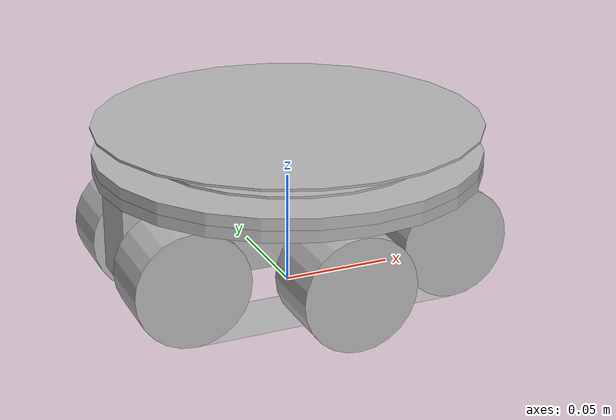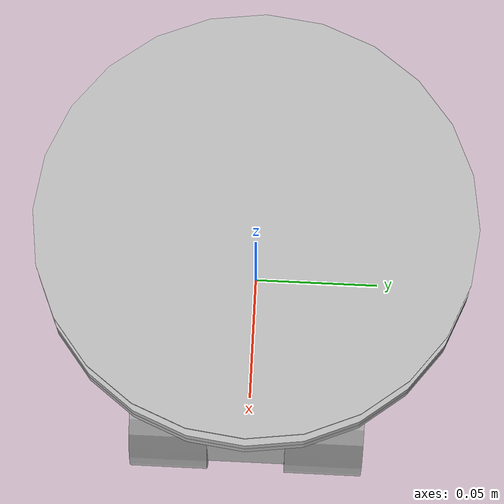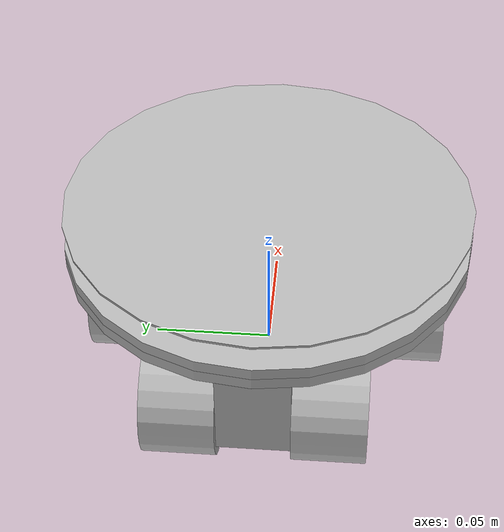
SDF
<?xml version='1.0'?>
<sdf version='1.6'>
		<model name="marXbot">
			<self_collide>true</self_collide>
			<pose>0.0 0.0 0.0 0.0 0.0 0.0</pose>
			<!-- Start of parts of the pmodel marXbot -->
				<!-- Start of declarations for part "marXbot::p1" -->
					<!-- Start of parts of part "marXbot::p1" -->
					<!-- Start of declarations for part "marXbot::p1::LTreel" -->
						<!-- Start of parts of part "marXbot::p1::LTreel" -->
						<!-- End of parts of part "marXbot::p1::LTreel" -->

						<!-- Start of links of part "marXbot::p1::LTreel" -->
						<!-- link full name is marXbot::p1::LTreel::Wheel -->
						<link name="1-Wheel">
								<pose>0.0 0.059999998530114576 0.024997220650460422 -1.5709353129016326 -0.0 0.0</pose>
								<inertial>
									<pose>0.0 0.0 0.0 0.0 0.0 0.0</pose>
									<inertia>
										<ixx>1.0</ixx>
										<ixy>0.0</ixy>
										<ixz>0.0</ixz>
										<iyy>1.0</iyy>
										<iyz>0.0</iyz>
										<izz>1.0</izz>
									</inertia>
									<mass>1.0</mass>
								</inertial>
								<!-- body full name is marXbot::p1::LTreel::Wheel::Wheel -->
								<collision name="1--Wheel">
									<laser_retro>0.0</laser_retro>
									<pose>0.0 0.0 0.0 0.0 0.0 0.0</pose>
									<geometry>
										<cylinder>
											<radius>0.025025001541152614</radius>
											<length>0.029999999329447746</length>
										</cylinder>
									</geometry>
									<surface>
										<bounce>
											<restitution_coefficient>0.0</restitution_coefficient>
											<threshold>100000.0</threshold>
										</bounce>
										<friction>
											<ode>
												<mu>1.0</mu>
												<mu2>1.0</mu2>
												<fdir1>0.0 0.0 0.0</fdir1>
												<slip1>0.0</slip1>
												<slip2>0.0</slip2>
											</ode>
											<torsional>
												<coefficient>1.0</coefficient>
												<surface_radius>0.0</surface_radius>
											</torsional>
										</friction>
									</surface>
								</collision>
								<visual name="1--Wheel">
									<laser_retro>0.0</laser_retro>
									<pose>0.0 0.0 0.0 0.0 0.0 0.0</pose>
									<geometry>
										<cylinder>
											<radius>0.025025001541152614</radius>
											<length>0.029999999329447746</length>
										</cylinder>
									</geometry>
									<surface>
										<bounce>
											<restitution_coefficient>0.0</restitution_coefficient>
											<threshold>100000.0</threshold>
										</bounce>
										<friction>
											<ode>
												<mu>1.0</mu>
												<mu2>1.0</mu2>
												<fdir1>0.0 0.0 0.0</fdir1>
												<slip1>0.0</slip1>
												<slip2>0.0</slip2>
											</ode>
											<torsional>
												<coefficient>1.0</coefficient>
												<surface_radius>0.0</surface_radius>
											</torsional>
										</friction>
									</surface>
								</visual>
						</link>
						<!-- link full name is marXbot::p1::LTreel::Track -->
						<link name="2-Track">
								<pose>0.0 0.029999999329447746 0.02500000037252903 3.1414999961853027 0.0 0.0</pose>
								<inertial>
									<pose>0.0 0.0 0.0 0.0 0.0 0.0</pose>
									<inertia>
										<ixx>1.0</ixx>
										<ixy>0.0</ixy>
										<ixz>0.0</ixz>
										<iyy>1.0</iyy>
										<iyz>0.0</iyz>
										<izz>1.0</izz>
									</inertia>
									<mass>1.0</mass>
								</inertial>
								<!-- body full name is marXbot::p1::LTreel::Track::Top -->
								<collision name="2--Top">
									<laser_retro>0.0</laser_retro>
									<pose>0.0 0.0 0.02500000037252903 0.0 0.0 0.0</pose>
									<geometry>
										<box>
											<size>0.12000000104308128 0.029999999329447746 0</size>
										</box>
									</geometry>
									<surface>
										<bounce>
											<restitution_coefficient>0.0</restitution_coefficient>
											<threshold>100000.0</threshold>
										</bounce>
										<friction>
											<ode>
												<mu>1.0</mu>
												<mu2>1.0</mu2>
												<fdir1>0.0 0.0 0.0</fdir1>
												<slip1>0.0</slip1>
												<slip2>0.0</slip2>
											</ode>
											<torsional>
												<coefficient>1.0</coefficient>
												<surface_radius>0.0</surface_radius>
											</torsional>
										</friction>
									</surface>
								</collision>
								<visual name="2--Top">
									<laser_retro>0.0</laser_retro>
									<pose>0.0 0.0 0.02500000037252903 0.0 0.0 0.0</pose>
									<geometry>
										<box>
											<size>0.12000000104308128 0.029999999329447746 0</size>
										</box>
									</geometry>
									<surface>
										<bounce>
											<restitution_coefficient>0.0</restitution_coefficient>
											<threshold>100000.0</threshold>
										</bounce>
										<friction>
											<ode>
												<mu>1.0</mu>
												<mu2>1.0</mu2>
												<fdir1>0.0 0.0 0.0</fdir1>
												<slip1>0.0</slip1>
												<slip2>0.0</slip2>
											</ode>
											<torsional>
												<coefficient>1.0</coefficient>
												<surface_radius>0.0</surface_radius>
											</torsional>
										</friction>
									</surface>
								</visual>
								<!-- body full name is marXbot::p1::LTreel::Track::Bottom -->
								<collision name="3--Bottom">
									<laser_retro>0.0</laser_retro>
									<pose>0.0 0.0 -0.02500000037252903 0.0 0.0 0.0</pose>
									<geometry>
										<box>
											<size>0.12000000104308128 0.029999999329447746 0</size>
										</box>
									</geometry>
									<surface>
										<bounce>
											<restitution_coefficient>0.0</restitution_coefficient>
											<threshold>100000.0</threshold>
										</bounce>
										<friction>
											<ode>
												<mu>1.0</mu>
												<mu2>1.0</mu2>
												<fdir1>0.0 0.0 0.0</fdir1>
												<slip1>0.0</slip1>
												<slip2>0.0</slip2>
											</ode>
											<torsional>
												<coefficient>1.0</coefficient>
												<surface_radius>0.0</surface_radius>
											</torsional>
										</friction>
									</surface>
								</collision>
								<visual name="3--Bottom">
									<laser_retro>0.0</laser_retro>
									<pose>0.0 0.0 -0.02500000037252903 0.0 0.0 0.0</pose>
									<geometry>
										<box>
											<size>0.12000000104308128 0.029999999329447746 0</size>
										</box>
									</geometry>
									<surface>
										<bounce>
											<restitution_coefficient>0.0</restitution_coefficient>
											<threshold>100000.0</threshold>
										</bounce>
										<friction>
											<ode>
												<mu>1.0</mu>
												<mu2>1.0</mu2>
												<fdir1>0.0 0.0 0.0</fdir1>
												<slip1>0.0</slip1>
												<slip2>0.0</slip2>
											</ode>
											<torsional>
												<coefficient>1.0</coefficient>
												<surface_radius>0.0</surface_radius>
											</torsional>
										</friction>
									</surface>
								</visual>
								<!-- body full name is marXbot::p1::LTreel::Track::FrontWheel -->
								<collision name="4--FrontWheel">
									<laser_retro>0.0</laser_retro>
									<pose>-0.06000000052154064 0.0 0.0 1.5707499980926514 0.0 0.0</pose>
									<geometry>
										<cylinder>
											<radius>0.02500000037252903</radius>
											<length>0.029999999329447746</length>
										</cylinder>
									</geometry>
									<surface>
										<bounce>
											<restitution_coefficient>0.0</restitution_coefficient>
											<threshold>100000.0</threshold>
										</bounce>
										<friction>
											<ode>
												<mu>1.0</mu>
												<mu2>1.0</mu2>
												<fdir1>0.0 0.0 0.0</fdir1>
												<slip1>0.0</slip1>
												<slip2>0.0</slip2>
											</ode>
											<torsional>
												<coefficient>1.0</coefficient>
												<surface_radius>0.0</surface_radius>
											</torsional>
										</friction>
									</surface>
								</collision>
								<visual name="4--FrontWheel">
									<laser_retro>0.0</laser_retro>
									<pose>-0.06000000052154064 0.0 0.0 1.5707499980926514 0.0 0.0</pose>
									<geometry>
										<cylinder>
											<radius>0.02500000037252903</radius>
											<length>0.029999999329447746</length>
										</cylinder>
									</geometry>
									<surface>
										<bounce>
											<restitution_coefficient>0.0</restitution_coefficient>
											<threshold>100000.0</threshold>
										</bounce>
										<friction>
											<ode>
												<mu>1.0</mu>
												<mu2>1.0</mu2>
												<fdir1>0.0 0.0 0.0</fdir1>
												<slip1>0.0</slip1>
												<slip2>0.0</slip2>
											</ode>
											<torsional>
												<coefficient>1.0</coefficient>
												<surface_radius>0.0</surface_radius>
											</torsional>
										</friction>
									</surface>
								</visual>
								<!-- body full name is marXbot::p1::LTreel::Track::BackWheel -->
								<collision name="5--BackWheel">
									<laser_retro>0.0</laser_retro>
									<pose>0.06000000052154064 0.0 0.0 1.5707499980926514 0.0 0.0</pose>
									<geometry>
										<cylinder>
											<radius>0.02500000037252903</radius>
											<length>0.029999999329447746</length>
										</cylinder>
									</geometry>
									<surface>
										<bounce>
											<restitution_coefficient>0.0</restitution_coefficient>
											<threshold>100000.0</threshold>
										</bounce>
										<friction>
											<ode>
												<mu>1.0</mu>
												<mu2>1.0</mu2>
												<fdir1>0.0 0.0 0.0</fdir1>
												<slip1>0.0</slip1>
												<slip2>0.0</slip2>
											</ode>
											<torsional>
												<coefficient>1.0</coefficient>
												<surface_radius>0.0</surface_radius>
											</torsional>
										</friction>
									</surface>
								</collision>
								<visual name="5--BackWheel">
									<laser_retro>0.0</laser_retro>
									<pose>0.06000000052154064 0.0 0.0 1.5707499980926514 0.0 0.0</pose>
									<geometry>
										<cylinder>
											<radius>0.02500000037252903</radius>
											<length>0.029999999329447746</length>
										</cylinder>
									</geometry>
									<surface>
										<bounce>
											<restitution_coefficient>0.0</restitution_coefficient>
											<threshold>100000.0</threshold>
										</bounce>
										<friction>
											<ode>
												<mu>1.0</mu>
												<mu2>1.0</mu2>
												<fdir1>0.0 0.0 0.0</fdir1>
												<slip1>0.0</slip1>
												<slip2>0.0</slip2>
											</ode>
											<torsional>
												<coefficient>1.0</coefficient>
												<surface_radius>0.0</surface_radius>
											</torsional>
										</friction>
									</surface>
								</visual>
						</link>
						<!-- End of links of part "marXbot::p1::LTreel" -->

						<!-- Start of joints of part "marXbot::p1::LTreel" -->
						<!-- End of joints of part "marXbot::p1::LTreel" -->

						<!-- Start of fixed connections of part "marXbot::p1::LTreel" -->

						<!-- End of fixed connections of part "marXbot::p1::LTreel" -->
					<!-- End of declarations for part "marXbot::p1::LTreel" -->
					<!-- Start of declarations for part "marXbot::p1::RTreel" -->
						<!-- Start of parts of part "marXbot::p1::RTreel" -->
						<!-- End of parts of part "marXbot::p1::RTreel" -->

						<!-- Start of links of part "marXbot::p1::RTreel" -->
						<!-- link full name is marXbot::p1::RTreel::Wheel -->
						<link name="3-Wheel">
								<pose>0.0 -0.05999999865889549 0.02500000037252903 1.5707499980926514 -0.0 0.0</pose>
								<inertial>
									<pose>0.0 0.0 0.0 0.0 0.0 0.0</pose>
									<inertia>
										<ixx>1.0</ixx>
										<ixy>0.0</ixy>
										<ixz>0.0</ixz>
										<iyy>1.0</iyy>
										<iyz>0.0</iyz>
										<izz>1.0</izz>
									</inertia>
									<mass>1.0</mass>
								</inertial>
								<!-- body full name is marXbot::p1::RTreel::Wheel::Wheel -->
								<collision name="6--Wheel">
									<laser_retro>0.0</laser_retro>
									<pose>0.0 0.0 0.0 0.0 0.0 0.0</pose>
									<geometry>
										<cylinder>
											<radius>0.025025001541152614</radius>
											<length>0.029999999329447746</length>
										</cylinder>
									</geometry>
									<surface>
										<bounce>
											<restitution_coefficient>0.0</restitution_coefficient>
											<threshold>100000.0</threshold>
										</bounce>
										<friction>
											<ode>
												<mu>1.0</mu>
												<mu2>1.0</mu2>
												<fdir1>0.0 0.0 0.0</fdir1>
												<slip1>0.0</slip1>
												<slip2>0.0</slip2>
											</ode>
											<torsional>
												<coefficient>1.0</coefficient>
												<surface_radius>0.0</surface_radius>
											</torsional>
										</friction>
									</surface>
								</collision>
								<visual name="6--Wheel">
									<laser_retro>0.0</laser_retro>
									<pose>0.0 0.0 0.0 0.0 0.0 0.0</pose>
									<geometry>
										<cylinder>
											<radius>0.025025001541152614</radius>
											<length>0.029999999329447746</length>
										</cylinder>
									</geometry>
									<surface>
										<bounce>
											<restitution_coefficient>0.0</restitution_coefficient>
											<threshold>100000.0</threshold>
										</bounce>
										<friction>
											<ode>
												<mu>1.0</mu>
												<mu2>1.0</mu2>
												<fdir1>0.0 0.0 0.0</fdir1>
												<slip1>0.0</slip1>
												<slip2>0.0</slip2>
											</ode>
											<torsional>
												<coefficient>1.0</coefficient>
												<surface_radius>0.0</surface_radius>
											</torsional>
										</friction>
									</surface>
								</visual>
						</link>
						<!-- link full name is marXbot::p1::RTreel::Track -->
						<link name="4-Track">
								<pose>0.0 -0.029999999329447746 0.02500000037252903 0.0 0.0 0.0</pose>
								<inertial>
									<pose>0.0 0.0 0.0 0.0 0.0 0.0</pose>
									<inertia>
										<ixx>1.0</ixx>
										<ixy>0.0</ixy>
										<ixz>0.0</ixz>
										<iyy>1.0</iyy>
										<iyz>0.0</iyz>
										<izz>1.0</izz>
									</inertia>
									<mass>1.0</mass>
								</inertial>
								<!-- body full name is marXbot::p1::RTreel::Track::Top -->
								<collision name="7--Top">
									<laser_retro>0.0</laser_retro>
									<pose>0.0 0.0 0.02500000037252903 0.0 0.0 0.0</pose>
									<geometry>
										<box>
											<size>0.12000000104308128 0.029999999329447746 0</size>
										</box>
									</geometry>
									<surface>
										<bounce>
											<restitution_coefficient>0.0</restitution_coefficient>
											<threshold>100000.0</threshold>
										</bounce>
										<friction>
											<ode>
												<mu>1.0</mu>
												<mu2>1.0</mu2>
												<fdir1>0.0 0.0 0.0</fdir1>
												<slip1>0.0</slip1>
												<slip2>0.0</slip2>
											</ode>
											<torsional>
												<coefficient>1.0</coefficient>
												<surface_radius>0.0</surface_radius>
											</torsional>
										</friction>
									</surface>
								</collision>
								<visual name="7--Top">
									<laser_retro>0.0</laser_retro>
									<pose>0.0 0.0 0.02500000037252903 0.0 0.0 0.0</pose>
									<geometry>
										<box>
											<size>0.12000000104308128 0.029999999329447746 0</size>
										</box>
									</geometry>
									<surface>
										<bounce>
											<restitution_coefficient>0.0</restitution_coefficient>
											<threshold>100000.0</threshold>
										</bounce>
										<friction>
											<ode>
												<mu>1.0</mu>
												<mu2>1.0</mu2>
												<fdir1>0.0 0.0 0.0</fdir1>
												<slip1>0.0</slip1>
												<slip2>0.0</slip2>
											</ode>
											<torsional>
												<coefficient>1.0</coefficient>
												<surface_radius>0.0</surface_radius>
											</torsional>
										</friction>
									</surface>
								</visual>
								<!-- body full name is marXbot::p1::RTreel::Track::Bottom -->
								<collision name="8--Bottom">
									<laser_retro>0.0</laser_retro>
									<pose>0.0 0.0 -0.02500000037252903 0.0 0.0 0.0</pose>
									<geometry>
										<box>
											<size>0.12000000104308128 0.029999999329447746 0</size>
										</box>
									</geometry>
									<surface>
										<bounce>
											<restitution_coefficient>0.0</restitution_coefficient>
											<threshold>100000.0</threshold>
										</bounce>
										<friction>
											<ode>
												<mu>1.0</mu>
												<mu2>1.0</mu2>
												<fdir1>0.0 0.0 0.0</fdir1>
												<slip1>0.0</slip1>
												<slip2>0.0</slip2>
											</ode>
											<torsional>
												<coefficient>1.0</coefficient>
												<surface_radius>0.0</surface_radius>
											</torsional>
										</friction>
									</surface>
								</collision>
								<visual name="8--Bottom">
									<laser_retro>0.0</laser_retro>
									<pose>0.0 0.0 -0.02500000037252903 0.0 0.0 0.0</pose>
									<geometry>
										<box>
											<size>0.12000000104308128 0.029999999329447746 0</size>
										</box>
									</geometry>
									<surface>
										<bounce>
											<restitution_coefficient>0.0</restitution_coefficient>
											<threshold>100000.0</threshold>
										</bounce>
										<friction>
											<ode>
												<mu>1.0</mu>
												<mu2>1.0</mu2>
												<fdir1>0.0 0.0 0.0</fdir1>
												<slip1>0.0</slip1>
												<slip2>0.0</slip2>
											</ode>
											<torsional>
												<coefficient>1.0</coefficient>
												<surface_radius>0.0</surface_radius>
											</torsional>
										</friction>
									</surface>
								</visual>
								<!-- body full name is marXbot::p1::RTreel::Track::FrontWheel -->
								<collision name="9--FrontWheel">
									<laser_retro>0.0</laser_retro>
									<pose>-0.06000000052154064 0.0 0.0 1.5707499980926514 0.0 0.0</pose>
									<geometry>
										<cylinder>
											<radius>0.02500000037252903</radius>
											<length>0.029999999329447746</length>
										</cylinder>
									</geometry>
									<surface>
										<bounce>
											<restitution_coefficient>0.0</restitution_coefficient>
											<threshold>100000.0</threshold>
										</bounce>
										<friction>
											<ode>
												<mu>1.0</mu>
												<mu2>1.0</mu2>
												<fdir1>0.0 0.0 0.0</fdir1>
												<slip1>0.0</slip1>
												<slip2>0.0</slip2>
											</ode>
											<torsional>
												<coefficient>1.0</coefficient>
												<surface_radius>0.0</surface_radius>
											</torsional>
										</friction>
									</surface>
								</collision>
								<visual name="9--FrontWheel">
									<laser_retro>0.0</laser_retro>
									<pose>-0.06000000052154064 0.0 0.0 1.5707499980926514 0.0 0.0</pose>
									<geometry>
										<cylinder>
											<radius>0.02500000037252903</radius>
											<length>0.029999999329447746</length>
										</cylinder>
									</geometry>
									<surface>
										<bounce>
											<restitution_coefficient>0.0</restitution_coefficient>
											<threshold>100000.0</threshold>
										</bounce>
										<friction>
											<ode>
												<mu>1.0</mu>
												<mu2>1.0</mu2>
												<fdir1>0.0 0.0 0.0</fdir1>
												<slip1>0.0</slip1>
												<slip2>0.0</slip2>
											</ode>
											<torsional>
												<coefficient>1.0</coefficient>
												<surface_radius>0.0</surface_radius>
											</torsional>
										</friction>
									</surface>
								</visual>
								<!-- body full name is marXbot::p1::RTreel::Track::BackWheel -->
								<collision name="10--BackWheel">
									<laser_retro>0.0</laser_retro>
									<pose>0.06000000052154064 0.0 0.0 1.5707499980926514 0.0 0.0</pose>
									<geometry>
										<cylinder>
											<radius>0.02500000037252903</radius>
											<length>0.029999999329447746</length>
										</cylinder>
									</geometry>
									<surface>
										<bounce>
											<restitution_coefficient>0.0</restitution_coefficient>
											<threshold>100000.0</threshold>
										</bounce>
										<friction>
											<ode>
												<mu>1.0</mu>
												<mu2>1.0</mu2>
												<fdir1>0.0 0.0 0.0</fdir1>
												<slip1>0.0</slip1>
												<slip2>0.0</slip2>
											</ode>
											<torsional>
												<coefficient>1.0</coefficient>
												<surface_radius>0.0</surface_radius>
											</torsional>
										</friction>
									</surface>
								</collision>
								<visual name="10--BackWheel">
									<laser_retro>0.0</laser_retro>
									<pose>0.06000000052154064 0.0 0.0 1.5707499980926514 0.0 0.0</pose>
									<geometry>
										<cylinder>
											<radius>0.02500000037252903</radius>
											<length>0.029999999329447746</length>
										</cylinder>
									</geometry>
									<surface>
										<bounce>
											<restitution_coefficient>0.0</restitution_coefficient>
											<threshold>100000.0</threshold>
										</bounce>
										<friction>
											<ode>
												<mu>1.0</mu>
												<mu2>1.0</mu2>
												<fdir1>0.0 0.0 0.0</fdir1>
												<slip1>0.0</slip1>
												<slip2>0.0</slip2>
											</ode>
											<torsional>
												<coefficient>1.0</coefficient>
												<surface_radius>0.0</surface_radius>
											</torsional>
										</friction>
									</surface>
								</visual>
						</link>
						<!-- End of links of part "marXbot::p1::RTreel" -->

						<!-- Start of joints of part "marXbot::p1::RTreel" -->
						<!-- End of joints of part "marXbot::p1::RTreel" -->

						<!-- Start of fixed connections of part "marXbot::p1::RTreel" -->

						<!-- End of fixed connections of part "marXbot::p1::RTreel" -->
					<!-- End of declarations for part "marXbot::p1::RTreel" -->
					<!-- End of parts of part "marXbot::p1" -->

					<!-- Start of links of part "marXbot::p1" -->
					<!-- link full name is marXbot::p1::Core -->
					<link name="5-Core">
							<pose>0.0 0.0 0.057500001043081284 0.0 0.0 0.0</pose>
							<inertial>
								<pose>0.0 0.0 0.0 0.0 0.0 0.0</pose>
								<inertia>
									<ixx>1.0</ixx>
									<ixy>0.0</ixy>
									<ixz>0.0</ixz>
									<iyy>1.0</iyy>
									<iyz>0.0</iyz>
									<izz>1.0</izz>
								</inertia>
								<mass>1.0</mass>
							</inertial>
							<!-- body full name is marXbot::p1::Core::Spine -->
							<collision name="11--Spine">
								<laser_retro>0.0</laser_retro>
								<pose>0.0 0.0 -0.02250000089406967 0.0 0.0 1.5707499980926514</pose>
								<geometry>
									<box>
										<size>0.029999999329447746 0.1599999964237213 0.03999999910593033</size>
									</box>
								</geometry>
								<surface>
									<bounce>
										<restitution_coefficient>0.0</restitution_coefficient>
										<threshold>100000.0</threshold>
									</bounce>
									<friction>
										<ode>
											<mu>1.0</mu>
											<mu2>1.0</mu2>
											<fdir1>0.0 0.0 0.0</fdir1>
											<slip1>0.0</slip1>
											<slip2>0.0</slip2>
										</ode>
										<torsional>
											<coefficient>1.0</coefficient>
											<surface_radius>0.0</surface_radius>
										</torsional>
									</friction>
								</surface>
							</collision>
							<visual name="11--Spine">
								<laser_retro>0.0</laser_retro>
								<pose>0.0 0.0 -0.02250000089406967 0.0 0.0 1.5707499980926514</pose>
								<geometry>
									<box>
										<size>0.029999999329447746 0.1599999964237213 0.03999999910593033</size>
									</box>
								</geometry>
								<surface>
									<bounce>
										<restitution_coefficient>0.0</restitution_coefficient>
										<threshold>100000.0</threshold>
									</bounce>
									<friction>
										<ode>
											<mu>1.0</mu>
											<mu2>1.0</mu2>
											<fdir1>0.0 0.0 0.0</fdir1>
											<slip1>0.0</slip1>
											<slip2>0.0</slip2>
										</ode>
										<torsional>
											<coefficient>1.0</coefficient>
											<surface_radius>0.0</surface_radius>
										</torsional>
									</friction>
								</surface>
							</visual>
							<!-- body full name is marXbot::p1::Core::Frame -->
							<collision name="12--Frame">
								<laser_retro>0.0</laser_retro>
								<pose>0.0 0.0 0.0 0.0 0.0 0.0</pose>
								<geometry>
									<cylinder>
										<radius>0.08500000089406967</radius>
										<length>0.004999999888241291</length>
									</cylinder>
								</geometry>
								<surface>
									<bounce>
										<restitution_coefficient>0.0</restitution_coefficient>
										<threshold>100000.0</threshold>
									</bounce>
									<friction>
										<ode>
											<mu>1.0</mu>
											<mu2>1.0</mu2>
											<fdir1>0.0 0.0 0.0</fdir1>
											<slip1>0.0</slip1>
											<slip2>0.0</slip2>
										</ode>
										<torsional>
											<coefficient>1.0</coefficient>
											<surface_radius>0.0</surface_radius>
										</torsional>
									</friction>
								</surface>
							</collision>
							<visual name="12--Frame">
								<laser_retro>0.0</laser_retro>
								<pose>0.0 0.0 0.0 0.0 0.0 0.0</pose>
								<geometry>
									<cylinder>
										<radius>0.08500000089406967</radius>
										<length>0.004999999888241291</length>
									</cylinder>
								</geometry>
								<surface>
									<bounce>
										<restitution_coefficient>0.0</restitution_coefficient>
										<threshold>100000.0</threshold>
									</bounce>
									<friction>
										<ode>
											<mu>1.0</mu>
											<mu2>1.0</mu2>
											<fdir1>0.0 0.0 0.0</fdir1>
											<slip1>0.0</slip1>
											<slip2>0.0</slip2>
										</ode>
										<torsional>
											<coefficient>1.0</coefficient>
											<surface_radius>0.0</surface_radius>
										</torsional>
									</friction>
								</surface>
							</visual>
							<!-- WARNING: The SDF generator relies on annotations of the sensor Proximity::0 to specify aspects of the
							sensor that are accounted for in the equations. -->
							<!-- sensor simple name is Proximity -->
							<sensor name="Proximity::0" type="ray">
								<pose>0.0 0.0 0.0 -0.0 1.57079632679 0.0</pose>
								<visualize>true</visualize>
								<always_on>true</always_on>
								<update_rate>1</update_rate>
								<ray>
									<scan>
										<horizontal>
											<samples>1</samples>
											<resolution>1.0</resolution>
										</horizontal>
										<vertical>
											<samples>1</samples>
											<resolution>1.0</resolution>
										</vertical>
									</scan>
									<range>
										<min>0.0</min>
										<max>0.10000000149011612</max>
									</range>
								</ray>
							</sensor>
							<!-- WARNING: The SDF generator relies on annotations of the sensor Proximity::1 to specify aspects of the
							sensor that are accounted for in the equations. -->
							<!-- sensor simple name is Proximity -->
							<sensor name="Proximity::1" type="ray">
								<pose>0.0 0.0 0.0 -0.2617916663487752 1.57079632679 0.0</pose>
								<visualize>true</visualize>
								<always_on>true</always_on>
								<update_rate>1</update_rate>
								<ray>
									<scan>
										<horizontal>
											<samples>1</samples>
											<resolution>1.0</resolution>
										</horizontal>
										<vertical>
											<samples>1</samples>
											<resolution>1.0</resolution>
										</vertical>
									</scan>
									<range>
										<min>0.0</min>
										<max>0.10000000149011612</max>
									</range>
								</ray>
							</sensor>
							<!-- WARNING: The SDF generator relies on annotations of the sensor Proximity::2 to specify aspects of the
							sensor that are accounted for in the equations. -->
							<!-- sensor simple name is Proximity -->
							<sensor name="Proximity::2" type="ray">
								<pose>0.0 0.0 0.0 -0.5235833326975504 1.57079632679 0.0</pose>
								<visualize>true</visualize>
								<always_on>true</always_on>
								<update_rate>1</update_rate>
								<ray>
									<scan>
										<horizontal>
											<samples>1</samples>
											<resolution>1.0</resolution>
										</horizontal>
										<vertical>
											<samples>1</samples>
											<resolution>1.0</resolution>
										</vertical>
									</scan>
									<range>
										<min>0.0</min>
										<max>0.10000000149011612</max>
									</range>
								</ray>
							</sensor>
							<!-- WARNING: The SDF generator relies on annotations of the sensor Proximity::3 to specify aspects of the
							sensor that are accounted for in the equations. -->
							<!-- sensor simple name is Proximity -->
							<sensor name="Proximity::3" type="ray">
								<pose>0.0 0.0 0.0 -0.7853749990463258 1.57079632679 0.0</pose>
								<visualize>true</visualize>
								<always_on>true</always_on>
								<update_rate>1</update_rate>
								<ray>
									<scan>
										<horizontal>
											<samples>1</samples>
											<resolution>1.0</resolution>
										</horizontal>
										<vertical>
											<samples>1</samples>
											<resolution>1.0</resolution>
										</vertical>
									</scan>
									<range>
										<min>0.0</min>
										<max>0.10000000149011612</max>
									</range>
								</ray>
							</sensor>
							<!-- WARNING: The SDF generator relies on annotations of the sensor Proximity::4 to specify aspects of the
							sensor that are accounted for in the equations. -->
							<!-- sensor simple name is Proximity -->
							<sensor name="Proximity::4" type="ray">
								<pose>0.0 0.0 0.0 -1.0471666653951008 1.57079632679 0.0</pose>
								<visualize>true</visualize>
								<always_on>true</always_on>
								<update_rate>1</update_rate>
								<ray>
									<scan>
										<horizontal>
											<samples>1</samples>
											<resolution>1.0</resolution>
										</horizontal>
										<vertical>
											<samples>1</samples>
											<resolution>1.0</resolution>
										</vertical>
									</scan>
									<range>
										<min>0.0</min>
										<max>0.10000000149011612</max>
									</range>
								</ray>
							</sensor>
							<!-- WARNING: The SDF generator relies on annotations of the sensor Proximity::5 to specify aspects of the
							sensor that are accounted for in the equations. -->
							<!-- sensor simple name is Proximity -->
							<sensor name="Proximity::5" type="ray">
								<pose>0.0 0.0 0.0 -1.3089583317438762 1.57079632679 0.0</pose>
								<visualize>true</visualize>
								<always_on>true</always_on>
								<update_rate>1</update_rate>
								<ray>
									<scan>
										<horizontal>
											<samples>1</samples>
											<resolution>1.0</resolution>
										</horizontal>
										<vertical>
											<samples>1</samples>
											<resolution>1.0</resolution>
										</vertical>
									</scan>
									<range>
										<min>0.0</min>
										<max>0.10000000149011612</max>
									</range>
								</ray>
							</sensor>
							<!-- WARNING: The SDF generator relies on annotations of the sensor Proximity::6 to specify aspects of the
							sensor that are accounted for in the equations. -->
							<!-- sensor simple name is Proximity -->
							<sensor name="Proximity::6" type="ray">
								<pose>0.0 0.0 0.0 -1.5707499980926514 1.57079632679 0.0</pose>
								<visualize>true</visualize>
								<always_on>true</always_on>
								<update_rate>1</update_rate>
								<ray>
									<scan>
										<horizontal>
											<samples>1</samples>
											<resolution>1.0</resolution>
										</horizontal>
										<vertical>
											<samples>1</samples>
											<resolution>1.0</resolution>
										</vertical>
									</scan>
									<range>
										<min>0.0</min>
										<max>0.10000000149011612</max>
									</range>
								</ray>
							</sensor>
							<!-- WARNING: The SDF generator relies on annotations of the sensor Proximity::7 to specify aspects of the
							sensor that are accounted for in the equations. -->
							<!-- sensor simple name is Proximity -->
							<sensor name="Proximity::7" type="ray">
								<pose>0.0 0.0 0.0 -1.8325416644414265 1.57079632679 0.0</pose>
								<visualize>true</visualize>
								<always_on>true</always_on>
								<update_rate>1</update_rate>
								<ray>
									<scan>
										<horizontal>
											<samples>1</samples>
											<resolution>1.0</resolution>
										</horizontal>
										<vertical>
											<samples>1</samples>
											<resolution>1.0</resolution>
										</vertical>
									</scan>
									<range>
										<min>0.0</min>
										<max>0.10000000149011612</max>
									</range>
								</ray>
							</sensor>
							<!-- WARNING: The SDF generator relies on annotations of the sensor Proximity::8 to specify aspects of the
							sensor that are accounted for in the equations. -->
							<!-- sensor simple name is Proximity -->
							<sensor name="Proximity::8" type="ray">
								<pose>0.0 0.0 0.0 -2.094333330790202 1.57079632679 0.0</pose>
								<visualize>true</visualize>
								<always_on>true</always_on>
								<update_rate>1</update_rate>
								<ray>
									<scan>
										<horizontal>
											<samples>1</samples>
											<resolution>1.0</resolution>
										</horizontal>
										<vertical>
											<samples>1</samples>
											<resolution>1.0</resolution>
										</vertical>
									</scan>
									<range>
										<min>0.0</min>
										<max>0.10000000149011612</max>
									</range>
								</ray>
							</sensor>
							<!-- WARNING: The SDF generator relies on annotations of the sensor Proximity::9 to specify aspects of the
							sensor that are accounted for in the equations. -->
							<!-- sensor simple name is Proximity -->
							<sensor name="Proximity::9" type="ray">
								<pose>0.0 0.0 0.0 -2.356124997138977 1.57079632679 0.0</pose>
								<visualize>true</visualize>
								<always_on>true</always_on>
								<update_rate>1</update_rate>
								<ray>
									<scan>
										<horizontal>
											<samples>1</samples>
											<resolution>1.0</resolution>
										</horizontal>
										<vertical>
											<samples>1</samples>
											<resolution>1.0</resolution>
										</vertical>
									</scan>
									<range>
										<min>0.0</min>
										<max>0.10000000149011612</max>
									</range>
								</ray>
							</sensor>
							<!-- WARNING: The SDF generator relies on annotations of the sensor Proximity::10 to specify aspects of the
							sensor that are accounted for in the equations. -->
							<!-- sensor simple name is Proximity -->
							<sensor name="Proximity::10" type="ray">
								<pose>0.0 0.0 0.0 -2.6179166634877524 1.57079632679 0.0</pose>
								<visualize>true</visualize>
								<always_on>true</always_on>
								<update_rate>1</update_rate>
								<ray>
									<scan>
										<horizontal>
											<samples>1</samples>
											<resolution>1.0</resolution>
										</horizontal>
										<vertical>
											<samples>1</samples>
											<resolution>1.0</resolution>
										</vertical>
									</scan>
									<range>
										<min>0.0</min>
										<max>0.10000000149011612</max>
									</range>
								</ray>
							</sensor>
							<!-- WARNING: The SDF generator relies on annotations of the sensor Proximity::11 to specify aspects of the
							sensor that are accounted for in the equations. -->
							<!-- sensor simple name is Proximity -->
							<sensor name="Proximity::11" type="ray">
								<pose>0.0 0.0 0.0 -2.8797083298365274 1.57079632679 0.0</pose>
								<visualize>true</visualize>
								<always_on>true</always_on>
								<update_rate>1</update_rate>
								<ray>
									<scan>
										<horizontal>
											<samples>1</samples>
											<resolution>1.0</resolution>
										</horizontal>
										<vertical>
											<samples>1</samples>
											<resolution>1.0</resolution>
										</vertical>
									</scan>
									<range>
										<min>0.0</min>
										<max>0.10000000149011612</max>
									</range>
								</ray>
							</sensor>
							<!-- WARNING: The SDF generator relies on annotations of the sensor Proximity::12 to specify aspects of the
							sensor that are accounted for in the equations. -->
							<!-- sensor simple name is Proximity -->
							<sensor name="Proximity::12" type="ray">
								<pose>0.0 0.0 0.0 -3.1414999961853027 1.57079632679 0.0</pose>
								<visualize>true</visualize>
								<always_on>true</always_on>
								<update_rate>1</update_rate>
								<ray>
									<scan>
										<horizontal>
											<samples>1</samples>
											<resolution>1.0</resolution>
										</horizontal>
										<vertical>
											<samples>1</samples>
											<resolution>1.0</resolution>
										</vertical>
									</scan>
									<range>
										<min>0.0</min>
										<max>0.10000000149011612</max>
									</range>
								</ray>
							</sensor>
							<!-- WARNING: The SDF generator relies on annotations of the sensor Proximity::13 to specify aspects of the
							sensor that are accounted for in the equations. -->
							<!-- sensor simple name is Proximity -->
							<sensor name="Proximity::13" type="ray">
								<pose>0.0 0.0 0.0 2.8798936446455086 1.57079632679 0.0</pose>
								<visualize>true</visualize>
								<always_on>true</always_on>
								<update_rate>1</update_rate>
								<ray>
									<scan>
										<horizontal>
											<samples>1</samples>
											<resolution>1.0</resolution>
										</horizontal>
										<vertical>
											<samples>1</samples>
											<resolution>1.0</resolution>
										</vertical>
									</scan>
									<range>
										<min>0.0</min>
										<max>0.10000000149011612</max>
									</range>
								</ray>
							</sensor>
							<!-- WARNING: The SDF generator relies on annotations of the sensor Proximity::14 to specify aspects of the
							sensor that are accounted for in the equations. -->
							<!-- sensor simple name is Proximity -->
							<sensor name="Proximity::14" type="ray">
								<pose>0.0 0.0 0.0 2.6181019782967336 1.57079632679 0.0</pose>
								<visualize>true</visualize>
								<always_on>true</always_on>
								<update_rate>1</update_rate>
								<ray>
									<scan>
										<horizontal>
											<samples>1</samples>
											<resolution>1.0</resolution>
										</horizontal>
										<vertical>
											<samples>1</samples>
											<resolution>1.0</resolution>
										</vertical>
									</scan>
									<range>
										<min>0.0</min>
										<max>0.10000000149011612</max>
									</range>
								</ray>
							</sensor>
							<!-- WARNING: The SDF generator relies on annotations of the sensor Proximity::15 to specify aspects of the
							sensor that are accounted for in the equations. -->
							<!-- sensor simple name is Proximity -->
							<sensor name="Proximity::15" type="ray">
								<pose>0.0 0.0 0.0 2.356310311947958 1.57079632679 0.0</pose>
								<visualize>true</visualize>
								<always_on>true</always_on>
								<update_rate>1</update_rate>
								<ray>
									<scan>
										<horizontal>
											<samples>1</samples>
											<resolution>1.0</resolution>
										</horizontal>
										<vertical>
											<samples>1</samples>
											<resolution>1.0</resolution>
										</vertical>
									</scan>
									<range>
										<min>0.0</min>
										<max>0.10000000149011612</max>
									</range>
								</ray>
							</sensor>
							<!-- WARNING: The SDF generator relies on annotations of the sensor Proximity::16 to specify aspects of the
							sensor that are accounted for in the equations. -->
							<!-- sensor simple name is Proximity -->
							<sensor name="Proximity::16" type="ray">
								<pose>0.0 0.0 0.0 2.0945186455991833 1.57079632679 0.0</pose>
								<visualize>true</visualize>
								<always_on>true</always_on>
								<update_rate>1</update_rate>
								<ray>
									<scan>
										<horizontal>
											<samples>1</samples>
											<resolution>1.0</resolution>
										</horizontal>
										<vertical>
											<samples>1</samples>
											<resolution>1.0</resolution>
										</vertical>
									</scan>
									<range>
										<min>0.0</min>
										<max>0.10000000149011612</max>
									</range>
								</ray>
							</sensor>
							<!-- WARNING: The SDF generator relies on annotations of the sensor Proximity::17 to specify aspects of the
							sensor that are accounted for in the equations. -->
							<!-- sensor simple name is Proximity -->
							<sensor name="Proximity::17" type="ray">
								<pose>0.0 0.0 0.0 1.8327269792504075 1.57079632679 0.0</pose>
								<visualize>true</visualize>
								<always_on>true</always_on>
								<update_rate>1</update_rate>
								<ray>
									<scan>
										<horizontal>
											<samples>1</samples>
											<resolution>1.0</resolution>
										</horizontal>
										<vertical>
											<samples>1</samples>
											<resolution>1.0</resolution>
										</vertical>
									</scan>
									<range>
										<min>0.0</min>
										<max>0.10000000149011612</max>
									</range>
								</ray>
							</sensor>
							<!-- WARNING: The SDF generator relies on annotations of the sensor Proximity::18 to specify aspects of the
							sensor that are accounted for in the equations. -->
							<!-- sensor simple name is Proximity -->
							<sensor name="Proximity::18" type="ray">
								<pose>0.0 0.0 0.0 1.5709353129016326 1.57079632679 0.0</pose>
								<visualize>true</visualize>
								<always_on>true</always_on>
								<update_rate>1</update_rate>
								<ray>
									<scan>
										<horizontal>
											<samples>1</samples>
											<resolution>1.0</resolution>
										</horizontal>
										<vertical>
											<samples>1</samples>
											<resolution>1.0</resolution>
										</vertical>
									</scan>
									<range>
										<min>0.0</min>
										<max>0.10000000149011612</max>
									</range>
								</ray>
							</sensor>
							<!-- WARNING: The SDF generator relies on annotations of the sensor Proximity::19 to specify aspects of the
							sensor that are accounted for in the equations. -->
							<!-- sensor simple name is Proximity -->
							<sensor name="Proximity::19" type="ray">
								<pose>0.0 0.0 0.0 1.3091436465528574 1.57079632679 0.0</pose>
								<visualize>true</visualize>
								<always_on>true</always_on>
								<update_rate>1</update_rate>
								<ray>
									<scan>
										<horizontal>
											<samples>1</samples>
											<resolution>1.0</resolution>
										</horizontal>
										<vertical>
											<samples>1</samples>
											<resolution>1.0</resolution>
										</vertical>
									</scan>
									<range>
										<min>0.0</min>
										<max>0.10000000149011612</max>
									</range>
								</ray>
							</sensor>
							<!-- WARNING: The SDF generator relies on annotations of the sensor Proximity::20 to specify aspects of the
							sensor that are accounted for in the equations. -->
							<!-- sensor simple name is Proximity -->
							<sensor name="Proximity::20" type="ray">
								<pose>0.0 0.0 0.0 1.0473519802040816 1.57079632679 0.0</pose>
								<visualize>true</visualize>
								<always_on>true</always_on>
								<update_rate>1</update_rate>
								<ray>
									<scan>
										<horizontal>
											<samples>1</samples>
											<resolution>1.0</resolution>
										</horizontal>
										<vertical>
											<samples>1</samples>
											<resolution>1.0</resolution>
										</vertical>
									</scan>
									<range>
										<min>0.0</min>
										<max>0.10000000149011612</max>
									</range>
								</ray>
							</sensor>
							<!-- WARNING: The SDF generator relies on annotations of the sensor Proximity::21 to specify aspects of the
							sensor that are accounted for in the equations. -->
							<!-- sensor simple name is Proximity -->
							<sensor name="Proximity::21" type="ray">
								<pose>0.0 0.0 0.0 0.7855603138553067 1.57079632679 0.0</pose>
								<visualize>true</visualize>
								<always_on>true</always_on>
								<update_rate>1</update_rate>
								<ray>
									<scan>
										<horizontal>
											<samples>1</samples>
											<resolution>1.0</resolution>
										</horizontal>
										<vertical>
											<samples>1</samples>
											<resolution>1.0</resolution>
										</vertical>
									</scan>
									<range>
										<min>0.0</min>
										<max>0.10000000149011612</max>
									</range>
								</ray>
							</sensor>
							<!-- WARNING: The SDF generator relies on annotations of the sensor Proximity::22 to specify aspects of the
							sensor that are accounted for in the equations. -->
							<!-- sensor simple name is Proximity -->
							<sensor name="Proximity::22" type="ray">
								<pose>0.0 0.0 0.0 0.5237686475065317 1.57079632679 0.0</pose>
								<visualize>true</visualize>
								<always_on>true</always_on>
								<update_rate>1</update_rate>
								<ray>
									<scan>
										<horizontal>
											<samples>1</samples>
											<resolution>1.0</resolution>
										</horizontal>
										<vertical>
											<samples>1</samples>
											<resolution>1.0</resolution>
										</vertical>
									</scan>
									<range>
										<min>0.0</min>
										<max>0.10000000149011612</max>
									</range>
								</ray>
							</sensor>
							<!-- WARNING: The SDF generator relies on annotations of the sensor Proximity::23 to specify aspects of the
							sensor that are accounted for in the equations. -->
							<!-- sensor simple name is Proximity -->
							<sensor name="Proximity::23" type="ray">
								<pose>0.0 0.0 0.0 0.2619769811577559 1.57079632679 0.0</pose>
								<visualize>true</visualize>
								<always_on>true</always_on>
								<update_rate>1</update_rate>
								<ray>
									<scan>
										<horizontal>
											<samples>1</samples>
											<resolution>1.0</resolution>
										</horizontal>
										<vertical>
											<samples>1</samples>
											<resolution>1.0</resolution>
										</vertical>
									</scan>
									<range>
										<min>0.0</min>
										<max>0.10000000149011612</max>
									</range>
								</ray>
							</sensor>
					</link>
					<!-- End of links of part "marXbot::p1" -->

					<!-- Start of joints of part "marXbot::p1" -->
					<!-- Full name of joint: marXbot::p1::Core::LHinge from marXbot::p1::Core to marXbot::p1::LTreel::Wheel-->
					<joint name="6-LHinge" type="revolute">
						<pose>0.0 1.3879983906672777E-6 -0.029999999297511393 1.5709353129016326 -0.0 0.0</pose>
						<parent>5-Core</parent>
						<child>1-Wheel</child>
						<!-- WARNING: The SDF generator relies on annotations of the joint 6-LHinge to specify in SDF aspects of the joint that are
							 accounted for in the equations. -->
						<axis>
							<initial_position>3.1414999961853027</initial_position>
							<xyz>0 1 0</xyz>
							<dynamics>
								<damping>0.0</damping>
								<friction>0.0</friction>
								<spring_reference>0.0</spring_reference>
								<spring_stiffness>0.0</spring_stiffness>
							</dynamics>
							<limit>
								<lower>-1.0000000272564224E16</lower>
								<upper>1.0000000272564224E16</upper>
								<effort>-1.0</effort>
								<velocity>-1.0</velocity>
								<stiffness>1.0E8</stiffness>
								<dissipation>1.0</dissipation>
							</limit>
						</axis>
					</joint>
					<!-- Full name of joint: marXbot::p1::Core::RHinge from marXbot::p1::Core to marXbot::p1::RTreel::Wheel-->
					<joint name="7-RHinge" type="revolute">
						<pose>0.0 1.391723680937984E-6 -0.02999999929716622 -1.5707499980926514 -0.0 0.0</pose>
						<parent>5-Core</parent>
						<child>3-Wheel</child>
						<!-- WARNING: The SDF generator relies on annotations of the joint 7-RHinge to specify in SDF aspects of the joint that are
							 accounted for in the equations. -->
						<axis>
							<initial_position>3.1414999961853027</initial_position>
							<xyz>0 -1 0</xyz>
							<dynamics>
								<damping>0.0</damping>
								<friction>0.0</friction>
								<spring_reference>0.0</spring_reference>
								<spring_stiffness>0.0</spring_stiffness>
							</dynamics>
							<limit>
								<lower>-1.0000000272564224E16</lower>
								<upper>1.0000000272564224E16</upper>
								<effort>-1.0</effort>
								<velocity>-1.0</velocity>
								<stiffness>1.0E8</stiffness>
								<dissipation>1.0</dissipation>
							</limit>
						</axis>
					</joint>
					<!-- End of joints of part "marXbot::p1" -->

					<!-- Start of fixed connections of part "marXbot::p1" -->
					<!-- fixed joint full name is marXbot::p1::Core::fixedJoint::marXbot::p2::Core from marXbot::p1::Core to marXbot::p2::Core -->
					<joint name="9-fixedJoint" type="fixed">
						<parent>5-Core</parent>
						<child>8-Core</child>
						<axis><xyz>0 0 1</xyz></axis>
					</joint>

					<!-- fixed joint full name is marXbot::p1::Core::fixedJoint::marXbot::p1::LTreel::Track from marXbot::p1::Core to marXbot::p1::LTreel::Track -->
					<joint name="10-fixedJoint" type="fixed">
						<parent>5-Core</parent>
						<child>2-Track</child>
						<axis><xyz>0 0 1</xyz></axis>
					</joint>
					<!-- fixed joint full name is marXbot::p1::Core::fixedJoint::marXbot::p1::RTreel::Track from marXbot::p1::Core to marXbot::p1::RTreel::Track -->
					<joint name="11-fixedJoint" type="fixed">
						<parent>5-Core</parent>
						<child>4-Track</child>
						<axis><xyz>0 0 1</xyz></axis>
					</joint>
					<!-- End of fixed connections of part "marXbot::p1" -->
				<!-- End of declarations for part "marXbot::p1" -->
				<!-- Start of declarations for part "marXbot::p2" -->
					<!-- Start of parts of part "marXbot::p2" -->
					<!-- End of parts of part "marXbot::p2" -->

					<!-- Start of links of part "marXbot::p2" -->
					<!-- link full name is marXbot::p2::Core -->
					<link name="8-Core">
							<pose>0.0 0.0 0.0625 0.0 -0.0 0.0</pose>
							<inertial>
								<pose>0.0 0.0 0.0 0.0 0.0 0.0</pose>
								<inertia>
									<ixx>1.0</ixx>
									<ixy>0.0</ixy>
									<ixz>0.0</ixz>
									<iyy>1.0</iyy>
									<iyz>0.0</iyz>
									<izz>1.0</izz>
								</inertia>
								<mass>0.009999999776482582</mass>
							</inertial>
							<!-- body full name is marXbot::p2::Core::Frame -->
							<collision name="13--Frame">
								<laser_retro>0.0</laser_retro>
								<pose>0.0 0.0 0.0 0.0 0.0 0.0</pose>
								<geometry>
									<cylinder>
										<radius>0.08500000089406967</radius>
										<length>0.004999999888241291</length>
									</cylinder>
								</geometry>
								<surface>
									<bounce>
										<restitution_coefficient>0.0</restitution_coefficient>
										<threshold>100000.0</threshold>
									</bounce>
									<friction>
										<ode>
											<mu>1.0</mu>
											<mu2>1.0</mu2>
											<fdir1>0.0 0.0 0.0</fdir1>
											<slip1>0.0</slip1>
											<slip2>0.0</slip2>
										</ode>
										<torsional>
											<coefficient>1.0</coefficient>
											<surface_radius>0.0</surface_radius>
										</torsional>
									</friction>
								</surface>
							</collision>
							<visual name="13--Frame">
								<laser_retro>0.0</laser_retro>
								<pose>0.0 0.0 0.0 0.0 0.0 0.0</pose>
								<geometry>
									<cylinder>
										<radius>0.08500000089406967</radius>
										<length>0.004999999888241291</length>
									</cylinder>
								</geometry>
								<surface>
									<bounce>
										<restitution_coefficient>0.0</restitution_coefficient>
										<threshold>100000.0</threshold>
									</bounce>
									<friction>
										<ode>
											<mu>1.0</mu>
											<mu2>1.0</mu2>
											<fdir1>0.0 0.0 0.0</fdir1>
											<slip1>0.0</slip1>
											<slip2>0.0</slip2>
										</ode>
										<torsional>
											<coefficient>1.0</coefficient>
											<surface_radius>0.0</surface_radius>
										</torsional>
									</friction>
								</surface>
							</visual>
							<!-- WARNING: The SDF generator relies on annotations of the sensor IRSensor::0 to specify aspects of the
							sensor that are accounted for in the equations. -->
							<!-- sensor simple name is IRSensor -->
							<sensor name="IRSensor::0" type="ray">
								<pose>0.0 0.0 0.0 -0.0 1.57079632679 0.0</pose>
								<visualize>true</visualize>
								<always_on>true</always_on>
								<update_rate>1</update_rate>
								<ray>
									<scan>
										<horizontal>
											<samples>1</samples>
											<resolution>1.0</resolution>
										</horizontal>
										<vertical>
											<samples>1</samples>
											<resolution>1.0</resolution>
										</vertical>
									</scan>
									<range>
										<min>0.0</min>
										<max>0.10000000149011612</max>
									</range>
								</ray>
							</sensor>
							<!-- WARNING: The SDF generator relies on annotations of the sensor IRSensor::1 to specify aspects of the
							sensor that are accounted for in the equations. -->
							<!-- sensor simple name is IRSensor -->
							<sensor name="IRSensor::1" type="ray">
								<pose>0.0 0.0 0.0 -0.7853749990463258 1.57079632679 0.0</pose>
								<visualize>true</visualize>
								<always_on>true</always_on>
								<update_rate>1</update_rate>
								<ray>
									<scan>
										<horizontal>
											<samples>1</samples>
											<resolution>1.0</resolution>
										</horizontal>
										<vertical>
											<samples>1</samples>
											<resolution>1.0</resolution>
										</vertical>
									</scan>
									<range>
										<min>0.0</min>
										<max>0.10000000149011612</max>
									</range>
								</ray>
							</sensor>
							<!-- WARNING: The SDF generator relies on annotations of the sensor IRSensor::2 to specify aspects of the
							sensor that are accounted for in the equations. -->
							<!-- sensor simple name is IRSensor -->
							<sensor name="IRSensor::2" type="ray">
								<pose>0.0 0.0 0.0 -1.5707499980926514 1.57079632679 0.0</pose>
								<visualize>true</visualize>
								<always_on>true</always_on>
								<update_rate>1</update_rate>
								<ray>
									<scan>
										<horizontal>
											<samples>1</samples>
											<resolution>1.0</resolution>
										</horizontal>
										<vertical>
											<samples>1</samples>
											<resolution>1.0</resolution>
										</vertical>
									</scan>
									<range>
										<min>0.0</min>
										<max>0.10000000149011612</max>
									</range>
								</ray>
							</sensor>
							<!-- WARNING: The SDF generator relies on annotations of the sensor IRSensor::3 to specify aspects of the
							sensor that are accounted for in the equations. -->
							<!-- sensor simple name is IRSensor -->
							<sensor name="IRSensor::3" type="ray">
								<pose>0.0 0.0 0.0 -2.356124997138977 1.57079632679 0.0</pose>
								<visualize>true</visualize>
								<always_on>true</always_on>
								<update_rate>1</update_rate>
								<ray>
									<scan>
										<horizontal>
											<samples>1</samples>
											<resolution>1.0</resolution>
										</horizontal>
										<vertical>
											<samples>1</samples>
											<resolution>1.0</resolution>
										</vertical>
									</scan>
									<range>
										<min>0.0</min>
										<max>0.10000000149011612</max>
									</range>
								</ray>
							</sensor>
							<!-- WARNING: The SDF generator relies on annotations of the sensor IRSensor::4 to specify aspects of the
							sensor that are accounted for in the equations. -->
							<!-- sensor simple name is IRSensor -->
							<sensor name="IRSensor::4" type="ray">
								<pose>0.0 0.0 0.0 -3.1414999961853027 1.57079632679 0.0</pose>
								<visualize>true</visualize>
								<always_on>true</always_on>
								<update_rate>1</update_rate>
								<ray>
									<scan>
										<horizontal>
											<samples>1</samples>
											<resolution>1.0</resolution>
										</horizontal>
										<vertical>
											<samples>1</samples>
											<resolution>1.0</resolution>
										</vertical>
									</scan>
									<range>
										<min>0.0</min>
										<max>0.10000000149011612</max>
									</range>
								</ray>
							</sensor>
							<!-- WARNING: The SDF generator relies on annotations of the sensor IRSensor::5 to specify aspects of the
							sensor that are accounted for in the equations. -->
							<!-- sensor simple name is IRSensor -->
							<sensor name="IRSensor::5" type="ray">
								<pose>0.0 0.0 0.0 2.356310311947958 1.57079632679 0.0</pose>
								<visualize>true</visualize>
								<always_on>true</always_on>
								<update_rate>1</update_rate>
								<ray>
									<scan>
										<horizontal>
											<samples>1</samples>
											<resolution>1.0</resolution>
										</horizontal>
										<vertical>
											<samples>1</samples>
											<resolution>1.0</resolution>
										</vertical>
									</scan>
									<range>
										<min>0.0</min>
										<max>0.10000000149011612</max>
									</range>
								</ray>
							</sensor>
							<!-- WARNING: The SDF generator relies on annotations of the sensor IRSensor::6 to specify aspects of the
							sensor that are accounted for in the equations. -->
							<!-- sensor simple name is IRSensor -->
							<sensor name="IRSensor::6" type="ray">
								<pose>0.0 0.0 0.0 1.5709353129016326 1.57079632679 0.0</pose>
								<visualize>true</visualize>
								<always_on>true</always_on>
								<update_rate>1</update_rate>
								<ray>
									<scan>
										<horizontal>
											<samples>1</samples>
											<resolution>1.0</resolution>
										</horizontal>
										<vertical>
											<samples>1</samples>
											<resolution>1.0</resolution>
										</vertical>
									</scan>
									<range>
										<min>0.0</min>
										<max>0.10000000149011612</max>
									</range>
								</ray>
							</sensor>
							<!-- WARNING: The SDF generator relies on annotations of the sensor IRSensor::7 to specify aspects of the
							sensor that are accounted for in the equations. -->
							<!-- sensor simple name is IRSensor -->
							<sensor name="IRSensor::7" type="ray">
								<pose>0.0 0.0 0.0 0.7855603138553067 1.57079632679 0.0</pose>
								<visualize>true</visualize>
								<always_on>true</always_on>
								<update_rate>1</update_rate>
								<ray>
									<scan>
										<horizontal>
											<samples>1</samples>
											<resolution>1.0</resolution>
										</horizontal>
										<vertical>
											<samples>1</samples>
											<resolution>1.0</resolution>
										</vertical>
									</scan>
									<range>
										<min>0.0</min>
										<max>0.10000000149011612</max>
									</range>
								</ray>
							</sensor>
					</link>
					<!-- End of links of part "marXbot::p2" -->

					<!-- Start of joints of part "marXbot::p2" -->
					<!-- End of joints of part "marXbot::p2" -->

					<!-- Start of fixed connections of part "marXbot::p2" -->
					<!-- fixed joint full name is marXbot::p2::Core::fixedJoint::marXbot::p3::Base from marXbot::p2::Core to marXbot::p3::Base -->
					<joint name="13-fixedJoint" type="fixed">
						<parent>8-Core</parent>
						<child>12-Base</child>
						<axis><xyz>0 0 1</xyz></axis>
					</joint>

					<!-- End of fixed connections of part "marXbot::p2" -->
				<!-- End of declarations for part "marXbot::p2" -->
				<!-- Start of declarations for part "marXbot::p3" -->
					<!-- Start of parts of part "marXbot::p3" -->
					<!-- Start of declarations for part "marXbot::p3::longrange::0" -->
						<!-- Start of parts of part "marXbot::p3::longrange::0" -->
						<!-- End of parts of part "marXbot::p3::longrange::0" -->

						<!-- Start of links of part "marXbot::p3::longrange::0" -->
						<!-- link full name is marXbot::p3::longrange::0::BBody -->
						<link name="14-BBody">
								<pose>0.0 0.0 0.07099999859929085 0.0 -0.0 0.0</pose>
								<inertial>
									<pose>0.0 0.0 0.0 0.0 0.0 0.0</pose>
									<inertia>
										<ixx>1.0</ixx>
										<ixy>0.0</ixy>
										<ixz>0.0</ixz>
										<iyy>1.0</iyy>
										<iyz>0.0</iyz>
										<izz>1.0</izz>
									</inertia>
									<mass>0.0010000000474974513</mass>
								</inertial>
								<!-- body full name is marXbot::p3::longrange::0::BBody::Box -->
								<collision name="14--Box">
									<laser_retro>0.0</laser_retro>
									<pose>0.0 0.0 0.0 0.0 0.0 0.0</pose>
									<geometry>
										<box>
											<size>0.00800000037997961 0.01600000075995922 0.00800000037997961</size>
										</box>
									</geometry>
									<surface>
										<bounce>
											<restitution_coefficient>0.0</restitution_coefficient>
											<threshold>100000.0</threshold>
										</bounce>
										<friction>
											<ode>
												<mu>1.0</mu>
												<mu2>1.0</mu2>
												<fdir1>0.0 0.0 0.0</fdir1>
												<slip1>0.0</slip1>
												<slip2>0.0</slip2>
											</ode>
											<torsional>
												<coefficient>1.0</coefficient>
												<surface_radius>0.0</surface_radius>
											</torsional>
										</friction>
									</surface>
								</collision>
								<visual name="14--Box">
									<laser_retro>0.0</laser_retro>
									<pose>0.0 0.0 0.0 0.0 0.0 0.0</pose>
									<geometry>
										<box>
											<size>0.00800000037997961 0.01600000075995922 0.00800000037997961</size>
										</box>
									</geometry>
									<surface>
										<bounce>
											<restitution_coefficient>0.0</restitution_coefficient>
											<threshold>100000.0</threshold>
										</bounce>
										<friction>
											<ode>
												<mu>1.0</mu>
												<mu2>1.0</mu2>
												<fdir1>0.0 0.0 0.0</fdir1>
												<slip1>0.0</slip1>
												<slip2>0.0</slip2>
											</ode>
											<torsional>
												<coefficient>1.0</coefficient>
												<surface_radius>0.0</surface_radius>
											</torsional>
										</friction>
									</surface>
								</visual>
								<!-- WARNING: The SDF generator relies on annotations of the sensor IRSensor to specify aspects of the
								sensor that are accounted for in the equations. -->
								<!-- sensor simple name is IRSensor -->
								<sensor name="IRSensor" type="ray">
									<pose>0.004000000189989805 -0.004000000189989805 0.0 -0.0 1.57079632679 0.0</pose>
									<visualize>true</visualize>
									<always_on>true</always_on>
									<update_rate>1</update_rate>
									<ray>
										<scan>
											<horizontal>
												<samples>1</samples>
												<resolution>1.0</resolution>
											</horizontal>
											<vertical>
												<samples>1</samples>
												<resolution>1.0</resolution>
											</vertical>
										</scan>
										<range>
											<min>0.0</min>
											<max>0.10000000149011612</max>
										</range>
									</ray>
								</sensor>
						</link>
						<!-- End of links of part "marXbot::p3::longrange::0" -->

						<!-- Start of joints of part "marXbot::p3::longrange::0" -->
						<!-- End of joints of part "marXbot::p3::longrange::0" -->

						<!-- Start of fixed connections of part "marXbot::p3::longrange::0" -->

						<!-- End of fixed connections of part "marXbot::p3::longrange::0" -->
					<!-- End of declarations for part "marXbot::p3::longrange::0" -->
					<!-- Start of declarations for part "marXbot::p3::longrange::1" -->
						<!-- Start of parts of part "marXbot::p3::longrange::1" -->
						<!-- End of parts of part "marXbot::p3::longrange::1" -->

						<!-- Start of links of part "marXbot::p3::longrange::1" -->
						<!-- link full name is marXbot::p3::longrange::1::BBody -->
						<link name="15-BBody">
								<pose>0.0 0.0 0.07099999859929085 0.0 -0.0 1.5707499980926514</pose>
								<inertial>
									<pose>0.0 0.0 0.0 0.0 0.0 0.0</pose>
									<inertia>
										<ixx>1.0</ixx>
										<ixy>0.0</ixy>
										<ixz>0.0</ixz>
										<iyy>1.0</iyy>
										<iyz>0.0</iyz>
										<izz>1.0</izz>
									</inertia>
									<mass>0.0010000000474974513</mass>
								</inertial>
								<!-- body full name is marXbot::p3::longrange::1::BBody::Box -->
								<collision name="15--Box">
									<laser_retro>0.0</laser_retro>
									<pose>0.0 0.0 0.0 0.0 0.0 0.0</pose>
									<geometry>
										<box>
											<size>0.00800000037997961 0.01600000075995922 0.00800000037997961</size>
										</box>
									</geometry>
									<surface>
										<bounce>
											<restitution_coefficient>0.0</restitution_coefficient>
											<threshold>100000.0</threshold>
										</bounce>
										<friction>
											<ode>
												<mu>1.0</mu>
												<mu2>1.0</mu2>
												<fdir1>0.0 0.0 0.0</fdir1>
												<slip1>0.0</slip1>
												<slip2>0.0</slip2>
											</ode>
											<torsional>
												<coefficient>1.0</coefficient>
												<surface_radius>0.0</surface_radius>
											</torsional>
										</friction>
									</surface>
								</collision>
								<visual name="15--Box">
									<laser_retro>0.0</laser_retro>
									<pose>0.0 0.0 0.0 0.0 0.0 0.0</pose>
									<geometry>
										<box>
											<size>0.00800000037997961 0.01600000075995922 0.00800000037997961</size>
										</box>
									</geometry>
									<surface>
										<bounce>
											<restitution_coefficient>0.0</restitution_coefficient>
											<threshold>100000.0</threshold>
										</bounce>
										<friction>
											<ode>
												<mu>1.0</mu>
												<mu2>1.0</mu2>
												<fdir1>0.0 0.0 0.0</fdir1>
												<slip1>0.0</slip1>
												<slip2>0.0</slip2>
											</ode>
											<torsional>
												<coefficient>1.0</coefficient>
												<surface_radius>0.0</surface_radius>
											</torsional>
										</friction>
									</surface>
								</visual>
								<!-- WARNING: The SDF generator relies on annotations of the sensor IRSensor to specify aspects of the
								sensor that are accounted for in the equations. -->
								<!-- sensor simple name is IRSensor -->
								<sensor name="IRSensor" type="ray">
									<pose>0.004000000189989805 -0.004000000189989805 0.0 -0.0 1.57079632679 0.0</pose>
									<visualize>true</visualize>
									<always_on>true</always_on>
									<update_rate>1</update_rate>
									<ray>
										<scan>
											<horizontal>
												<samples>1</samples>
												<resolution>1.0</resolution>
											</horizontal>
											<vertical>
												<samples>1</samples>
												<resolution>1.0</resolution>
											</vertical>
										</scan>
										<range>
											<min>0.0</min>
											<max>0.10000000149011612</max>
										</range>
									</ray>
								</sensor>
						</link>
						<!-- End of links of part "marXbot::p3::longrange::1" -->

						<!-- Start of joints of part "marXbot::p3::longrange::1" -->
						<!-- End of joints of part "marXbot::p3::longrange::1" -->

						<!-- Start of fixed connections of part "marXbot::p3::longrange::1" -->

						<!-- End of fixed connections of part "marXbot::p3::longrange::1" -->
					<!-- End of declarations for part "marXbot::p3::longrange::1" -->
					<!-- Start of declarations for part "marXbot::p3::longrange::2" -->
						<!-- Start of parts of part "marXbot::p3::longrange::2" -->
						<!-- End of parts of part "marXbot::p3::longrange::2" -->

						<!-- Start of links of part "marXbot::p3::longrange::2" -->
						<!-- link full name is marXbot::p3::longrange::2::BBody -->
						<link name="16-BBody">
								<pose>0.0 0.0 0.07099999859929085 0.0 -0.0 3.1414999961853027</pose>
								<inertial>
									<pose>0.0 0.0 0.0 0.0 0.0 0.0</pose>
									<inertia>
										<ixx>1.0</ixx>
										<ixy>0.0</ixy>
										<ixz>0.0</ixz>
										<iyy>1.0</iyy>
										<iyz>0.0</iyz>
										<izz>1.0</izz>
									</inertia>
									<mass>0.0010000000474974513</mass>
								</inertial>
								<!-- body full name is marXbot::p3::longrange::2::BBody::Box -->
								<collision name="16--Box">
									<laser_retro>0.0</laser_retro>
									<pose>0.0 0.0 0.0 0.0 0.0 0.0</pose>
									<geometry>
										<box>
											<size>0.00800000037997961 0.01600000075995922 0.00800000037997961</size>
										</box>
									</geometry>
									<surface>
										<bounce>
											<restitution_coefficient>0.0</restitution_coefficient>
											<threshold>100000.0</threshold>
										</bounce>
										<friction>
											<ode>
												<mu>1.0</mu>
												<mu2>1.0</mu2>
												<fdir1>0.0 0.0 0.0</fdir1>
												<slip1>0.0</slip1>
												<slip2>0.0</slip2>
											</ode>
											<torsional>
												<coefficient>1.0</coefficient>
												<surface_radius>0.0</surface_radius>
											</torsional>
										</friction>
									</surface>
								</collision>
								<visual name="16--Box">
									<laser_retro>0.0</laser_retro>
									<pose>0.0 0.0 0.0 0.0 0.0 0.0</pose>
									<geometry>
										<box>
											<size>0.00800000037997961 0.01600000075995922 0.00800000037997961</size>
										</box>
									</geometry>
									<surface>
										<bounce>
											<restitution_coefficient>0.0</restitution_coefficient>
											<threshold>100000.0</threshold>
										</bounce>
										<friction>
											<ode>
												<mu>1.0</mu>
												<mu2>1.0</mu2>
												<fdir1>0.0 0.0 0.0</fdir1>
												<slip1>0.0</slip1>
												<slip2>0.0</slip2>
											</ode>
											<torsional>
												<coefficient>1.0</coefficient>
												<surface_radius>0.0</surface_radius>
											</torsional>
										</friction>
									</surface>
								</visual>
								<!-- WARNING: The SDF generator relies on annotations of the sensor IRSensor to specify aspects of the
								sensor that are accounted for in the equations. -->
								<!-- sensor simple name is IRSensor -->
								<sensor name="IRSensor" type="ray">
									<pose>0.004000000189989805 -0.004000000189989805 0.0 -0.0 1.57079632679 0.0</pose>
									<visualize>true</visualize>
									<always_on>true</always_on>
									<update_rate>1</update_rate>
									<ray>
										<scan>
											<horizontal>
												<samples>1</samples>
												<resolution>1.0</resolution>
											</horizontal>
											<vertical>
												<samples>1</samples>
												<resolution>1.0</resolution>
											</vertical>
										</scan>
										<range>
											<min>0.0</min>
											<max>0.10000000149011612</max>
										</range>
									</ray>
								</sensor>
						</link>
						<!-- End of links of part "marXbot::p3::longrange::2" -->

						<!-- Start of joints of part "marXbot::p3::longrange::2" -->
						<!-- End of joints of part "marXbot::p3::longrange::2" -->

						<!-- Start of fixed connections of part "marXbot::p3::longrange::2" -->

						<!-- End of fixed connections of part "marXbot::p3::longrange::2" -->
					<!-- End of declarations for part "marXbot::p3::longrange::2" -->
					<!-- Start of declarations for part "marXbot::p3::longrange::3" -->
						<!-- Start of parts of part "marXbot::p3::longrange::3" -->
						<!-- End of parts of part "marXbot::p3::longrange::3" -->

						<!-- Start of links of part "marXbot::p3::longrange::3" -->
						<!-- link full name is marXbot::p3::longrange::3::BBody -->
						<link name="17-BBody">
								<pose>0.0 0.0 0.07099999859929085 0.0 -0.0 -1.5709353129016326</pose>
								<inertial>
									<pose>0.0 0.0 0.0 0.0 0.0 0.0</pose>
									<inertia>
										<ixx>1.0</ixx>
										<ixy>0.0</ixy>
										<ixz>0.0</ixz>
										<iyy>1.0</iyy>
										<iyz>0.0</iyz>
										<izz>1.0</izz>
									</inertia>
									<mass>0.0010000000474974513</mass>
								</inertial>
								<!-- body full name is marXbot::p3::longrange::3::BBody::Box -->
								<collision name="17--Box">
									<laser_retro>0.0</laser_retro>
									<pose>0.0 0.0 0.0 0.0 0.0 0.0</pose>
									<geometry>
										<box>
											<size>0.00800000037997961 0.01600000075995922 0.00800000037997961</size>
										</box>
									</geometry>
									<surface>
										<bounce>
											<restitution_coefficient>0.0</restitution_coefficient>
											<threshold>100000.0</threshold>
										</bounce>
										<friction>
											<ode>
												<mu>1.0</mu>
												<mu2>1.0</mu2>
												<fdir1>0.0 0.0 0.0</fdir1>
												<slip1>0.0</slip1>
												<slip2>0.0</slip2>
											</ode>
											<torsional>
												<coefficient>1.0</coefficient>
												<surface_radius>0.0</surface_radius>
											</torsional>
										</friction>
									</surface>
								</collision>
								<visual name="17--Box">
									<laser_retro>0.0</laser_retro>
									<pose>0.0 0.0 0.0 0.0 0.0 0.0</pose>
									<geometry>
										<box>
											<size>0.00800000037997961 0.01600000075995922 0.00800000037997961</size>
										</box>
									</geometry>
									<surface>
										<bounce>
											<restitution_coefficient>0.0</restitution_coefficient>
											<threshold>100000.0</threshold>
										</bounce>
										<friction>
											<ode>
												<mu>1.0</mu>
												<mu2>1.0</mu2>
												<fdir1>0.0 0.0 0.0</fdir1>
												<slip1>0.0</slip1>
												<slip2>0.0</slip2>
											</ode>
											<torsional>
												<coefficient>1.0</coefficient>
												<surface_radius>0.0</surface_radius>
											</torsional>
										</friction>
									</surface>
								</visual>
								<!-- WARNING: The SDF generator relies on annotations of the sensor IRSensor to specify aspects of the
								sensor that are accounted for in the equations. -->
								<!-- sensor simple name is IRSensor -->
								<sensor name="IRSensor" type="ray">
									<pose>0.004000000189989805 -0.004000000189989805 0.0 -0.0 1.57079632679 0.0</pose>
									<visualize>true</visualize>
									<always_on>true</always_on>
									<update_rate>1</update_rate>
									<ray>
										<scan>
											<horizontal>
												<samples>1</samples>
												<resolution>1.0</resolution>
											</horizontal>
											<vertical>
												<samples>1</samples>
												<resolution>1.0</resolution>
											</vertical>
										</scan>
										<range>
											<min>0.0</min>
											<max>0.10000000149011612</max>
										</range>
									</ray>
								</sensor>
						</link>
						<!-- End of links of part "marXbot::p3::longrange::3" -->

						<!-- Start of joints of part "marXbot::p3::longrange::3" -->
						<!-- End of joints of part "marXbot::p3::longrange::3" -->

						<!-- Start of fixed connections of part "marXbot::p3::longrange::3" -->

						<!-- End of fixed connections of part "marXbot::p3::longrange::3" -->
					<!-- End of declarations for part "marXbot::p3::longrange::3" -->
					<!-- End of parts of part "marXbot::p3" -->

					<!-- Start of links of part "marXbot::p3" -->
					<!-- link full name is marXbot::p3::Base -->
					<link name="12-Base">
							<pose>0.0 0.0 0.06549999862909317 0.0 -0.0 0.0</pose>
							<inertial>
								<pose>0.0 0.0 0.0 0.0 0.0 0.0</pose>
								<inertia>
									<ixx>1.0</ixx>
									<ixy>0.0</ixy>
									<ixz>0.0</ixz>
									<iyy>1.0</iyy>
									<iyz>0.0</iyz>
									<izz>1.0</izz>
								</inertia>
								<mass>0.009999999776482582</mass>
							</inertial>
							<!-- body full name is marXbot::p3::Base::Frame -->
							<collision name="18--Frame">
								<laser_retro>0.0</laser_retro>
								<pose>0.0 0.0 0.0 0.0 0.0 0.0</pose>
								<geometry>
									<cylinder>
										<radius>0.06499999761581421</radius>
										<length>0.0010000000474974513</length>
									</cylinder>
								</geometry>
								<surface>
									<bounce>
										<restitution_coefficient>0.0</restitution_coefficient>
										<threshold>100000.0</threshold>
									</bounce>
									<friction>
										<ode>
											<mu>1.0</mu>
											<mu2>1.0</mu2>
											<fdir1>0.0 0.0 0.0</fdir1>
											<slip1>0.0</slip1>
											<slip2>0.0</slip2>
										</ode>
										<torsional>
											<coefficient>1.0</coefficient>
											<surface_radius>0.0</surface_radius>
										</torsional>
									</friction>
								</surface>
							</collision>
							<visual name="18--Frame">
								<laser_retro>0.0</laser_retro>
								<pose>0.0 0.0 0.0 0.0 0.0 0.0</pose>
								<geometry>
									<cylinder>
										<radius>0.06499999761581421</radius>
										<length>0.0010000000474974513</length>
									</cylinder>
								</geometry>
								<surface>
									<bounce>
										<restitution_coefficient>0.0</restitution_coefficient>
										<threshold>100000.0</threshold>
									</bounce>
									<friction>
										<ode>
											<mu>1.0</mu>
											<mu2>1.0</mu2>
											<fdir1>0.0 0.0 0.0</fdir1>
											<slip1>0.0</slip1>
											<slip2>0.0</slip2>
										</ode>
										<torsional>
											<coefficient>1.0</coefficient>
											<surface_radius>0.0</surface_radius>
										</torsional>
									</friction>
								</surface>
							</visual>
					</link>
					<!-- link full name is marXbot::p3::Core -->
					<link name="18-Core">
							<pose>0.0 0.0 0.07099999859929085 0.0 -0.0 0.0</pose>
							<inertial>
								<pose>0.0 0.0 0.0 0.0 0.0 0.0</pose>
								<inertia>
									<ixx>1.0</ixx>
									<ixy>0.0</ixy>
									<ixz>0.0</ixz>
									<iyy>1.0</iyy>
									<iyz>0.0</iyz>
									<izz>1.0</izz>
								</inertia>
								<mass>1.0</mass>
							</inertial>
							<!-- body full name is marXbot::p3::Core::Spine -->
							<collision name="19--Spine">
								<laser_retro>0.0</laser_retro>
								<pose>0.0 0.0 0.0 0.0 0.0 0.0</pose>
								<geometry>
									<cylinder>
										<radius>0.03999999910593033</radius>
										<length>0.009999999776482582</length>
									</cylinder>
								</geometry>
								<surface>
									<bounce>
										<restitution_coefficient>0.0</restitution_coefficient>
										<threshold>100000.0</threshold>
									</bounce>
									<friction>
										<ode>
											<mu>1.0</mu>
											<mu2>1.0</mu2>
											<fdir1>0.0 0.0 0.0</fdir1>
											<slip1>0.0</slip1>
											<slip2>0.0</slip2>
										</ode>
										<torsional>
											<coefficient>1.0</coefficient>
											<surface_radius>0.0</surface_radius>
										</torsional>
									</friction>
								</surface>
							</collision>
							<visual name="19--Spine">
								<laser_retro>0.0</laser_retro>
								<pose>0.0 0.0 0.0 0.0 0.0 0.0</pose>
								<geometry>
									<cylinder>
										<radius>0.03999999910593033</radius>
										<length>0.009999999776482582</length>
									</cylinder>
								</geometry>
								<surface>
									<bounce>
										<restitution_coefficient>0.0</restitution_coefficient>
										<threshold>100000.0</threshold>
									</bounce>
									<friction>
										<ode>
											<mu>1.0</mu>
											<mu2>1.0</mu2>
											<fdir1>0.0 0.0 0.0</fdir1>
											<slip1>0.0</slip1>
											<slip2>0.0</slip2>
										</ode>
										<torsional>
											<coefficient>1.0</coefficient>
											<surface_radius>0.0</surface_radius>
										</torsional>
									</friction>
								</surface>
							</visual>
							<!-- body full name is marXbot::p3::Core::Top -->
							<collision name="20--Top">
								<laser_retro>0.0</laser_retro>
								<pose>0.0 0.0 0.005499999970197678 0.0 0.0 0.0</pose>
								<geometry>
									<cylinder>
										<radius>0.08500000089406967</radius>
										<length>0.0010000000474974513</length>
									</cylinder>
								</geometry>
								<surface>
									<bounce>
										<restitution_coefficient>0.0</restitution_coefficient>
										<threshold>100000.0</threshold>
									</bounce>
									<friction>
										<ode>
											<mu>1.0</mu>
											<mu2>1.0</mu2>
											<fdir1>0.0 0.0 0.0</fdir1>
											<slip1>0.0</slip1>
											<slip2>0.0</slip2>
										</ode>
										<torsional>
											<coefficient>1.0</coefficient>
											<surface_radius>0.0</surface_radius>
										</torsional>
									</friction>
								</surface>
							</collision>
							<visual name="20--Top">
								<laser_retro>0.0</laser_retro>
								<pose>0.0 0.0 0.005499999970197678 0.0 0.0 0.0</pose>
								<geometry>
									<cylinder>
										<radius>0.08500000089406967</radius>
										<length>0.0010000000474974513</length>
									</cylinder>
								</geometry>
								<surface>
									<bounce>
										<restitution_coefficient>0.0</restitution_coefficient>
										<threshold>100000.0</threshold>
									</bounce>
									<friction>
										<ode>
											<mu>1.0</mu>
											<mu2>1.0</mu2>
											<fdir1>0.0 0.0 0.0</fdir1>
											<slip1>0.0</slip1>
											<slip2>0.0</slip2>
										</ode>
										<torsional>
											<coefficient>1.0</coefficient>
											<surface_radius>0.0</surface_radius>
										</torsional>
									</friction>
								</surface>
							</visual>
					</link>
					<!-- End of links of part "marXbot::p3" -->

					<!-- Start of joints of part "marXbot::p3" -->
					<!-- Full name of joint: marXbot::p3::Base::rj from marXbot::p3::Base to marXbot::p3::Core-->
					<joint name="19-rj" type="revolute">
						<pose>0.0 0.0 -0.005499999970197678 0.0 -0.0 0.0</pose>
						<parent>12-Base</parent>
						<child>18-Core</child>
						<!-- WARNING: The SDF generator relies on annotations of the joint 19-rj to specify in SDF aspects of the joint that are
							 accounted for in the equations. -->
						<axis>
							<xyz>0 0 1</xyz>
						</axis>
					</joint>
					<!-- End of joints of part "marXbot::p3" -->

					<!-- Start of fixed connections of part "marXbot::p3" -->

					<!-- fixed joint full name is marXbot::p3::Core::fixedJoint::marXbot::p3::longrange::1::BBody from marXbot::p3::Core to marXbot::p3::longrange::1::BBody -->
					<joint name="20-fixedJoint" type="fixed">
						<parent>18-Core</parent>
						<child>15-BBody</child>
						<axis><xyz>0 0 1</xyz></axis>
					</joint>
					<!-- fixed joint full name is marXbot::p3::Core::fixedJoint::marXbot::p3::longrange::0::BBody from marXbot::p3::Core to marXbot::p3::longrange::0::BBody -->
					<joint name="21-fixedJoint" type="fixed">
						<parent>18-Core</parent>
						<child>14-BBody</child>
						<axis><xyz>0 0 1</xyz></axis>
					</joint>
					<!-- fixed joint full name is marXbot::p3::Core::fixedJoint::marXbot::p3::longrange::3::BBody from marXbot::p3::Core to marXbot::p3::longrange::3::BBody -->
					<joint name="22-fixedJoint" type="fixed">
						<parent>18-Core</parent>
						<child>17-BBody</child>
						<axis><xyz>0 0 1</xyz></axis>
					</joint>
					<!-- fixed joint full name is marXbot::p3::Core::fixedJoint::marXbot::p3::longrange::2::BBody from marXbot::p3::Core to marXbot::p3::longrange::2::BBody -->
					<joint name="23-fixedJoint" type="fixed">
						<parent>18-Core</parent>
						<child>16-BBody</child>
						<axis><xyz>0 0 1</xyz></axis>
					</joint>
					<!-- End of fixed connections of part "marXbot::p3" -->
				<!-- End of declarations for part "marXbot::p3" -->
			<!-- End of parts of the pmodel marXbot -->

			<!-- Start of links of the pmodel marXbot -->
			<!-- End of links of the pmodel marXbot -->

			<!-- Start of joints of the pmodel marXbot -->
			<!-- End of joints of the pmodel marXbot -->

			<!-- Start of fixed connections of the pmodel marXbot -->
			<!-- End of fixed connections of the pmodel marXbot -->
		</model>
</sdf>
